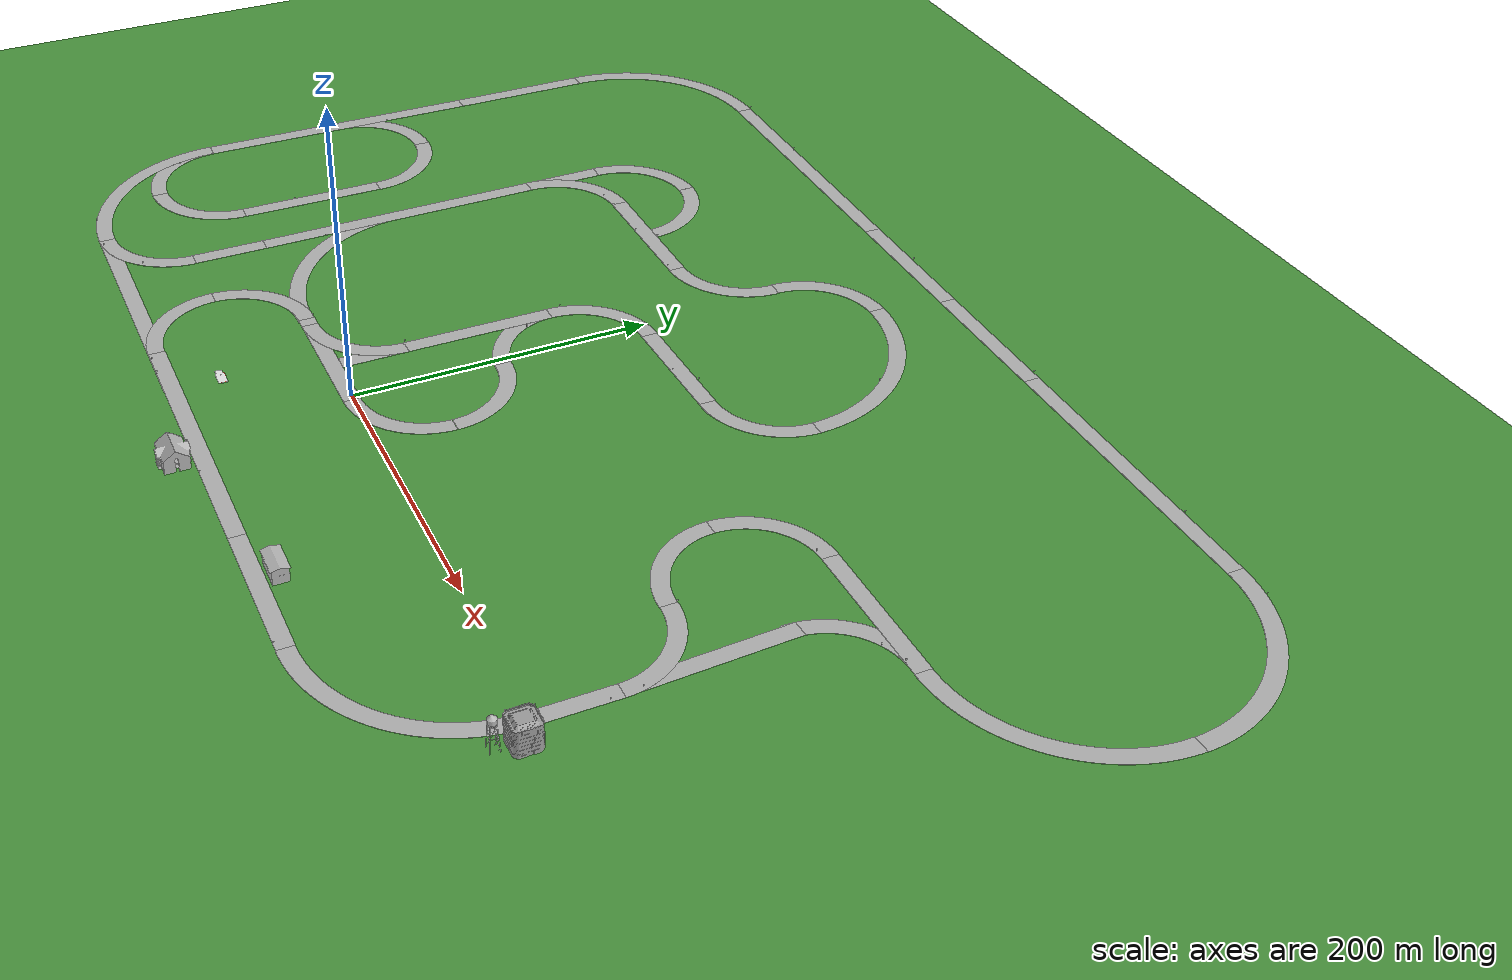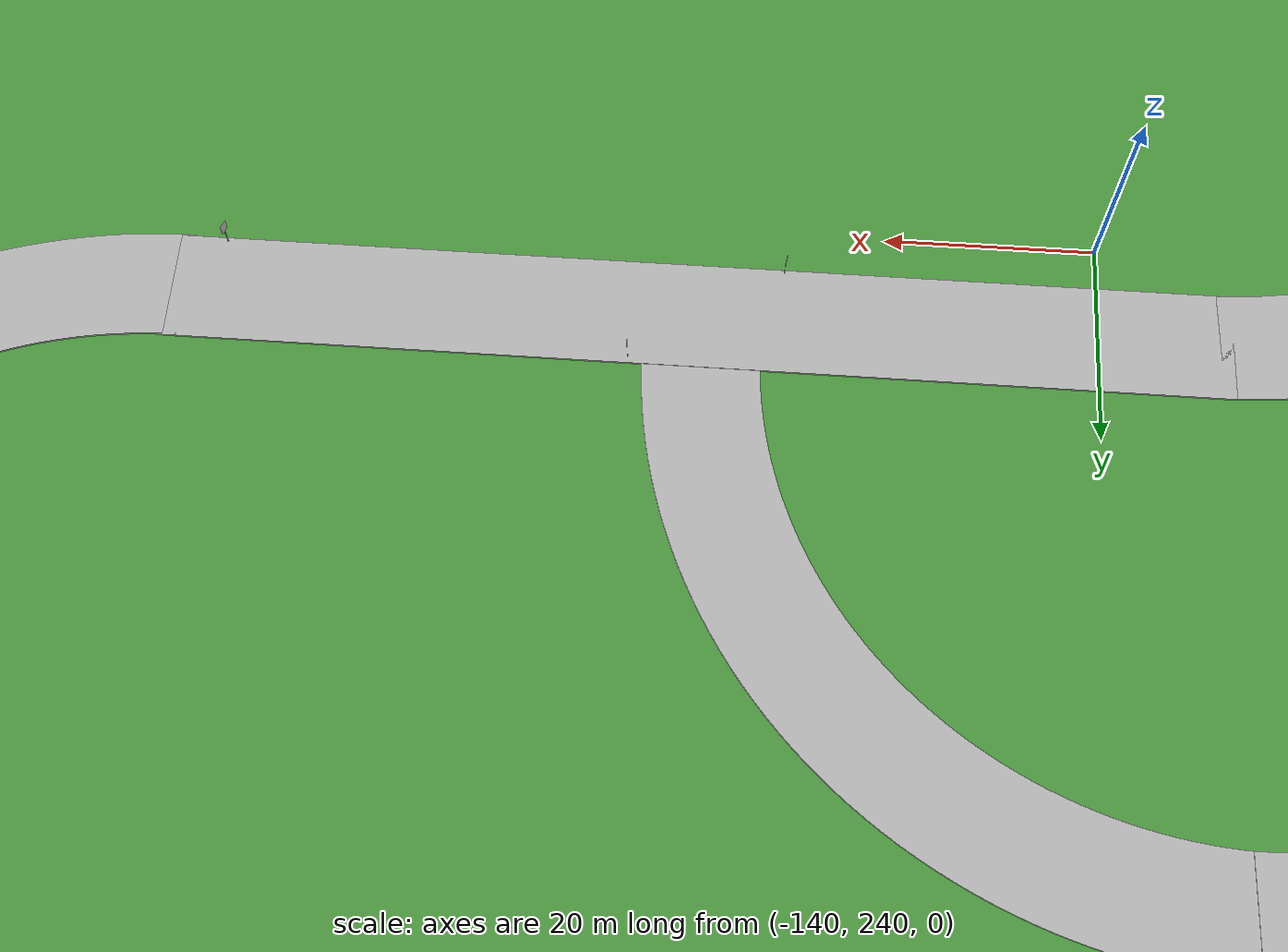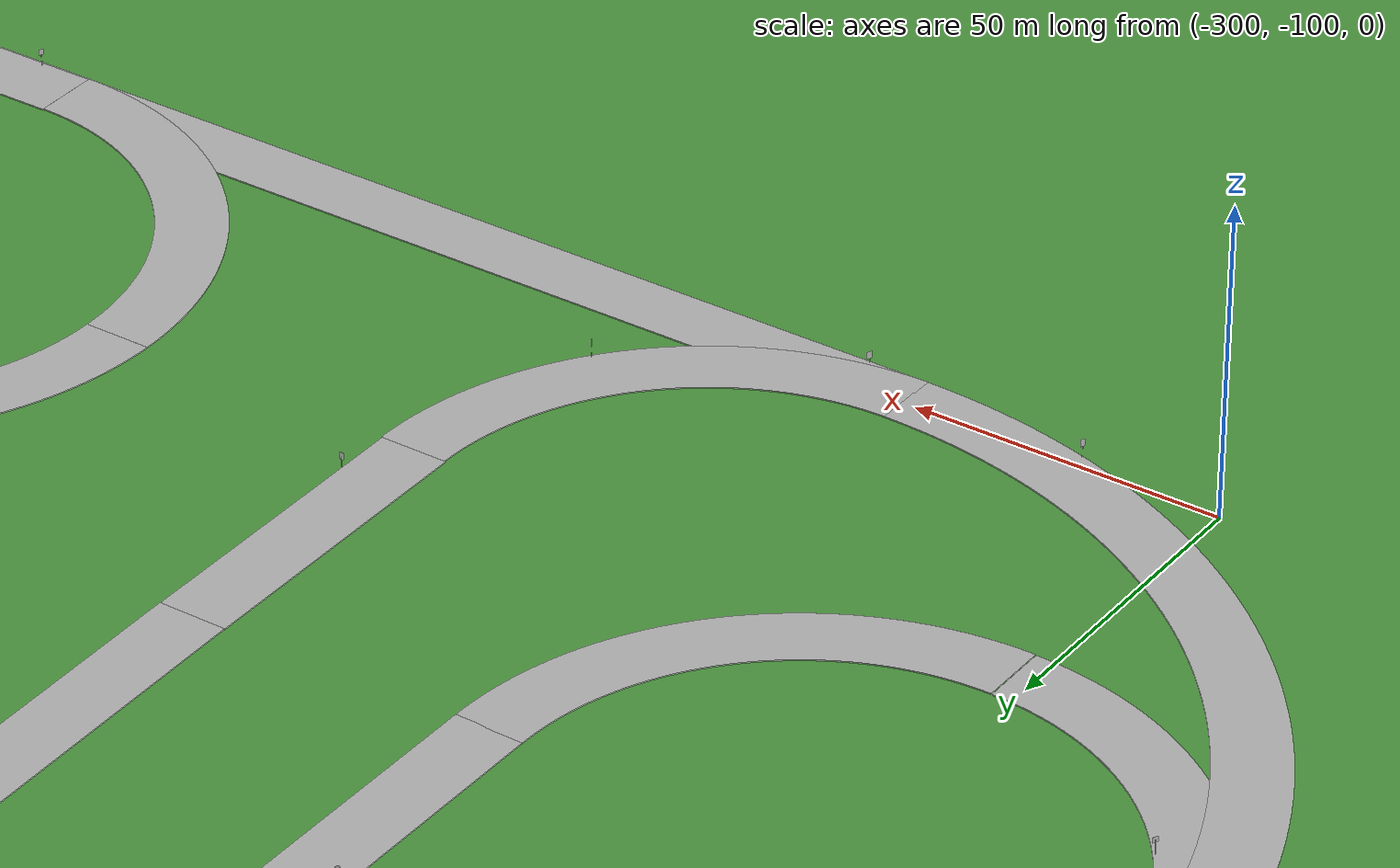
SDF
<sdf version="1.6">
 <world name="default">
  <light name="sun" type="directional">
   <pose>0 0 10 0 -0 0</pose>
   <diffuse>0.8 0.8 0.8 1</diffuse>
   <specular>0.2 0.2 0.2 1</specular>
   <attenuation>
    <range>1000</range>
    <constant>0.9</constant>
    <linear>0.01</linear>
    <quadratic>0.001</quadratic>
   </attenuation>
   <direction>-0.5 0.1 -0.9</direction>
  </light>
  <gravity>0 0 -9.8</gravity>
  <magnetic_field>6e-06 2.3e-05 -4.2e-05</magnetic_field>
  <atmosphere type="adiabatic"/>
  <physics name="default_physics" default="0" type="ode">
   <max_step_size>0.001</max_step_size>
   <real_time_factor>1</real_time_factor>
   <real_time_update_rate>1000</real_time_update_rate>
  </physics>
  <scene><ambient>0.4 0.4 0.4 1</ambient><background>0.7 0.7 0.7 1</background><shadows>1</shadows></scene>
  <audio><device>default</device></audio>
  <spherical_coordinates>
   <surface_model>EARTH_WGS84</surface_model>
   <latitude_deg>0</latitude_deg>
   <longitude_deg>0</longitude_deg>
   <elevation>0</elevation>
   <heading_deg>0</heading_deg>
  </spherical_coordinates>
  <model name="ground_plane">
   <static>1</static>
   <link name="link">
    <collision name="collision">
     <geometry><plane><normal>0 0 1</normal><size>10000 10000</size></plane></geometry>
     <surface><friction><ode><mu>100</mu><mu2>50</mu2></ode></friction></surface>
    </collision>
    <visual name="visual">
     <cast_shadows>0</cast_shadows>
     <geometry><plane><normal>0 0 1</normal><size>10000 10000</size></plane></geometry>
     <material>
      <script>
       <uri>model://ds_grass_background/materials/scripts</uri>
       <uri>model://ds_grass_background/materials/textures</uri>
       <name>GrassBackground</name>
      </script>
     </material>
    </visual>
    <velocity_decay><linear>0</linear><angular>0</angular></velocity_decay>
   </link>
  </model>
  <model name="Gas Station">
   <static>1</static>
   <link name="link">
    <collision name="collision">
     <geometry><mesh><uri>model://gas_station/meshes/gas_station.dae</uri></mesh></geometry>
    </collision>
    <visual name="visual">
     <geometry><mesh><uri>model://gas_station/meshes/gas_station.dae</uri></mesh></geometry>
     <material>
      <script>
       <uri>model://gas_station/materials/scripts</uri>
       <uri>model://gas_station/materials/textures</uri>
       <name>GasStation/Diffuse</name>
      </script>
      <shader type="normal_map_object_space"><normal_map>GasStation_Normal.png</normal_map></shader>
     </material>
    </visual>
   </link>
   <pose>-47.8817 -70.5161 0 0 -0 0</pose>
  </model>
  <model name="(DS) Straight Road - 200m_8">
   <static>1</static>
   <link name="link">
    <inertial>
     <mass>1</mass>
     <inertia><ixx>1</ixx><iyy>1</iyy><izz>1</izz><ixy>0</ixy><ixz>0</ixz><iyz>0</iyz></inertia>
    </inertial>
    <collision name="collision">
     <geometry><mesh><uri>model://ds_straight_road_200m/meshes/straight_road_200m.dae</uri></mesh></geometry>
    </collision>
    <visual name="visual">
     <geometry><mesh><uri>model://ds_straight_road_200m/meshes/straight_road_200m.dae</uri></mesh></geometry>
    </visual>
   </link>
   <pose>4.98041 -90.7828 0 0 -0 0</pose>
  </model>
  <model name="(DS) Straight Road - 100m_0">
   <static>1</static>
   <link name="link">
    <inertial>
     <mass>1</mass>
     <inertia><ixx>1</ixx><iyy>1</iyy><izz>1</izz><ixy>0</ixy><ixz>0</ixz><iyz>0</iyz></inertia>
    </inertial>
    <collision name="collision">
     <geometry><mesh><uri>model://ds_straight_road_100m/meshes/straight_road_100m.dae</uri></mesh></geometry>
    </collision>
    <visual name="visual">
     <geometry><mesh><uri>model://ds_straight_road_100m/meshes/straight_road_100m.dae</uri></mesh></geometry>
    </visual>
   </link>
   <pose>154.969 -90.7906 0 0 -0 0</pose>
  </model>
  <model name="(DS) Curved Road - 100m_3">
   <static>1</static>
   <link name="link">
    <inertial>
     <mass>1</mass>
     <inertia><ixx>1</ixx><iyy>1</iyy><izz>1</izz><ixy>0</ixy><ixz>0</ixz><iyz>0</iyz></inertia>
    </inertial>
    <collision name="collision">
     <geometry><mesh><uri>model://ds_curved_road_100m/meshes/curved_road_100m.dae</uri></mesh></geometry>
    </collision>
    <visual name="visual">
     <geometry><mesh><uri>model://ds_curved_road_100m/meshes/curved_road_100m.dae</uri></mesh></geometry>
    </visual>
   </link>
   <pose>257.705 -53.7644 0 0 -0 0</pose>
  </model>
  <model name="(DS) Straight Road - 50m">
   <static>1</static>
   <link name="link">
    <inertial>
     <mass>1</mass>
     <inertia><ixx>1</ixx><iyy>1</iyy><izz>1</izz><ixy>0</ixy><ixz>0</ixz><iyz>0</iyz></inertia>
    </inertial>
    <collision name="collision">
     <geometry><mesh><uri>model://ds_straight_road_50m/meshes/straight_road_50m.dae</uri></mesh></geometry>
    </collision>
    <visual name="visual">
     <geometry><mesh><uri>model://ds_straight_road_50m/meshes/straight_road_50m.dae</uri></mesh></geometry>
    </visual>
   </link>
   <pose>314.936 23.9712 0 0 0 -1.5707</pose>
  </model>
  <model name="(DS) Curved Road - 100m_7">
   <static>1</static>
   <link name="link">
    <inertial>
     <mass>1</mass>
     <inertia><ixx>1</ixx><iyy>1</iyy><izz>1</izz><ixy>0</ixy><ixz>0</ixz><iyz>0</iyz></inertia>
    </inertial>
    <collision name="collision">
     <geometry><mesh><uri>model://ds_curved_road_100m/meshes/curved_road_100m.dae</uri></mesh></geometry>
    </collision>
    <visual name="visual">
     <geometry><mesh><uri>model://ds_curved_road_100m/meshes/curved_road_100m.dae</uri></mesh></geometry>
    </visual>
   </link>
   <pose>-300.462 -53.7388 0 0 0 -1.5707</pose>
  </model>
  <model name="(DS) Straight Road - 50m_2">
   <static>1</static>
   <link name="link">
    <inertial>
     <mass>1</mass>
     <inertia><ixx>1</ixx><iyy>1</iyy><izz>1</izz><ixy>0</ixy><ixz>0</ixz><iyz>0</iyz></inertia>
    </inertial>
    <collision name="collision">
     <geometry><mesh><uri>model://ds_straight_road_50m/meshes/straight_road_50m.dae</uri></mesh></geometry>
    </collision>
    <visual name="visual">
     <geometry><mesh><uri>model://ds_straight_road_50m/meshes/straight_road_50m.dae</uri></mesh></geometry>
    </visual>
   </link>
   <pose>-208.133 -26.0849 0 0 -0 1.5707</pose>
  </model>
  <model name="(DS) Curved Road - 50m_1">
   <static>1</static>
   <link name="link">
    <inertial>
     <mass>1</mass>
     <inertia><ixx>1</ixx><iyy>1</iyy><izz>1</izz><ixy>0</ixy><ixz>0</ixz><iyz>0</iyz></inertia>
    </inertial>
    <collision name="collision">
     <geometry><mesh><uri>model://ds_curved_road_50m/meshes/curved_road_50m.dae</uri></mesh></geometry>
    </collision>
    <visual name="visual">
     <geometry><mesh><uri>model://ds_curved_road_50m/meshes/curved_road_50m.dae</uri></mesh></geometry>
    </visual>
   </link>
   <pose>-267.119 125.372 0 0 -0 1.5517</pose>
  </model>
  <model name="(DS) Curved Road - 50m_7">
   <static>1</static>
   <link name="link">
    <inertial>
     <mass>1</mass>
     <inertia><ixx>1</ixx><iyy>1</iyy><izz>1</izz><ixy>0</ixy><ixz>0</ixz><iyz>0</iyz></inertia>
    </inertial>
    <collision name="collision">
     <geometry><mesh><uri>model://ds_curved_road_50m/meshes/curved_road_50m.dae</uri></mesh></geometry>
    </collision>
    <visual name="visual">
     <geometry><mesh><uri>model://ds_curved_road_50m/meshes/curved_road_50m.dae</uri></mesh></geometry>
    </visual>
   </link>
   <pose>282.694 76.6819 0 0 -0 1.5707</pose>
  </model>
  <model name="(DS) Curved Road - 50m_8">
   <static>1</static>
   <link name="link">
    <inertial>
     <mass>1</mass>
     <inertia><ixx>1</ixx><iyy>1</iyy><izz>1</izz><ixy>0</ixy><ixz>0</ixz><iyz>0</iyz></inertia>
    </inertial>
    <collision name="collision">
     <geometry><mesh><uri>model://ds_curved_road_50m/meshes/curved_road_50m.dae</uri></mesh></geometry>
    </collision>
    <visual name="visual">
     <geometry><mesh><uri>model://ds_curved_road_50m/meshes/curved_road_50m.dae</uri></mesh></geometry>
    </visual>
   </link>
   <pose>227.233 176.317 0 0 -0 3.14159</pose>
  </model>
  <model name="(DS) Curved Road - 50m_9">
   <static>1</static>
   <link name="link">
    <inertial>
     <mass>1</mass>
     <inertia><ixx>1</ixx><iyy>1</iyy><izz>1</izz><ixy>0</ixy><ixz>0</ixz><iyz>0</iyz></inertia>
    </inertial>
    <collision name="collision">
     <geometry><mesh><uri>model://ds_curved_road_50m/meshes/curved_road_50m.dae</uri></mesh></geometry>
    </collision>
    <visual name="visual">
     <geometry><mesh><uri>model://ds_curved_road_50m/meshes/curved_road_50m.dae</uri></mesh></geometry>
    </visual>
   </link>
   <pose>227.236 120.969 0 0 0 -1.5707</pose>
  </model>
  <model name="(DS) Straight Road - 100m_6">
   <static>1</static>
   <link name="link">
    <inertial>
     <mass>1</mass>
     <inertia><ixx>1</ixx><iyy>1</iyy><izz>1</izz><ixy>0</ixy><ixz>0</ixz><iyz>0</iyz></inertia>
    </inertial>
    <collision name="collision">
     <geometry><mesh><uri>model://ds_straight_road_100m/meshes/straight_road_100m.dae</uri></mesh></geometry>
    </collision>
    <visual name="visual">
     <geometry><mesh><uri>model://ds_straight_road_100m/meshes/straight_road_100m.dae</uri></mesh></geometry>
    </visual>
   </link>
   <pose>304.773 208.555 0 0 -0 0</pose>
  </model>
  <model name="(DS) Curved Road - 100m_8">
   <static>1</static>
   <link name="link">
    <inertial>
     <mass>1</mass>
     <inertia><ixx>1</ixx><iyy>1</iyy><izz>1</izz><ixy>0</ixy><ixz>0</ixz><iyz>0</iyz></inertia>
    </inertial>
    <collision name="collision">
     <geometry><mesh><uri>model://ds_curved_road_100m/meshes/curved_road_100m.dae</uri></mesh></geometry>
    </collision>
    <visual name="visual">
     <geometry><mesh><uri>model://ds_curved_road_100m/meshes/curved_road_100m.dae</uri></mesh></geometry>
    </visual>
   </link>
   <pose>407.453 245.59 0 0 -0 0</pose>
  </model>
  <model name="(DS) Curved Road - 100m_10">
   <static>1</static>
   <link name="link">
    <inertial>
     <mass>1</mass>
     <inertia><ixx>1</ixx><iyy>1</iyy><izz>1</izz><ixy>0</ixy><ixz>0</ixz><iyz>0</iyz></inertia>
    </inertial>
    <collision name="collision">
     <geometry><mesh><uri>model://ds_curved_road_100m/meshes/curved_road_100m.dae</uri></mesh></geometry>
    </collision>
    <visual name="visual">
     <geometry><mesh><uri>model://ds_curved_road_100m/meshes/curved_road_100m.dae</uri></mesh></geometry>
    </visual>
   </link>
   <pose>-297.976 351.025 0 0 -0 3.14153</pose>
  </model>
  <model name="(DS) Curved Road - 100m_11">
   <static>1</static>
   <link name="link">
    <inertial>
     <mass>1</mass>
     <inertia><ixx>1</ixx><iyy>1</iyy><izz>1</izz><ixy>0</ixy><ixz>0</ixz><iyz>0</iyz></inertia>
    </inertial>
    <collision name="collision">
     <geometry><mesh><uri>model://ds_curved_road_100m/meshes/curved_road_100m.dae</uri></mesh></geometry>
    </collision>
    <visual name="visual">
     <geometry><mesh><uri>model://ds_curved_road_100m/meshes/curved_road_100m.dae</uri></mesh></geometry>
    </visual>
   </link>
   <pose>407.577 351.04 0 0 -0 1.5707</pose>
  </model>
  <model name="(DS) Straight Road - 200m_9">
   <static>1</static>
   <link name="link">
    <inertial>
     <mass>1</mass>
     <inertia><ixx>1</ixx><iyy>1</iyy><izz>1</izz><ixy>0</ixy><ixz>0</ixz><iyz>0</iyz></inertia>
    </inertial>
    <collision name="collision">
     <geometry><mesh><uri>model://ds_straight_road_200m/meshes/straight_road_200m.dae</uri></mesh></geometry>
    </collision>
    <visual name="visual">
     <geometry><mesh><uri>model://ds_straight_road_200m/meshes/straight_road_200m.dae</uri></mesh></geometry>
    </visual>
   </link>
   <pose>-145.191 408.281 0 0 -0 0</pose>
  </model>
  <model name="(DS) Straight Road - 200m_11">
   <static>1</static>
   <link name="link">
    <inertial>
     <mass>1</mass>
     <inertia><ixx>1</ixx><iyy>1</iyy><izz>1</izz><ixy>0</ixy><ixz>0</ixz><iyz>0</iyz></inertia>
    </inertial>
    <collision name="collision">
     <geometry><mesh><uri>model://ds_straight_road_200m/meshes/straight_road_200m.dae</uri></mesh></geometry>
    </collision>
    <visual name="visual">
     <geometry><mesh><uri>model://ds_straight_road_200m/meshes/straight_road_200m.dae</uri></mesh></geometry>
    </visual>
   </link>
   <pose>254.821 408.288 0 0 -0 0</pose>
  </model>
  <model name="(DS) Curved Road - 50m_12">
   <static>1</static>
   <link name="link">
    <inertial>
     <mass>1</mass>
     <inertia><ixx>1</ixx><iyy>1</iyy><izz>1</izz><ixy>0</ixy><ixz>0</ixz><iyz>0</iyz></inertia>
    </inertial>
    <collision name="collision">
     <geometry><mesh><uri>model://ds_curved_road_50m/meshes/curved_road_50m.dae</uri></mesh></geometry>
    </collision>
    <visual name="visual">
     <geometry><mesh><uri>model://ds_curved_road_50m/meshes/curved_road_50m.dae</uri></mesh></geometry>
    </visual>
   </link>
   <pose>18.1266 326.932 0 0 -0 3.13988</pose>
  </model>
  <model name="(DS) Straight Road - 100m_8">
   <static>1</static>
   <link name="link">
    <inertial>
     <mass>1</mass>
     <inertia><ixx>1</ixx><iyy>1</iyy><izz>1</izz><ixy>0</ixy><ixz>0</ixz><iyz>0</iyz></inertia>
    </inertial>
    <collision name="collision">
     <geometry><mesh><uri>model://ds_straight_road_100m/meshes/straight_road_100m.dae</uri></mesh></geometry>
    </collision>
    <visual name="visual">
     <geometry><mesh><uri>model://ds_straight_road_100m/meshes/straight_road_100m.dae</uri></mesh></geometry>
    </visual>
   </link>
   <pose>55.7639 209.318 -0.024663 0 -0 0.020634</pose>
  </model>
  <model name="speed_25">
   <link name="link">
    <collision name="collision">
     <geometry><mesh><scale>1 1 1</scale><uri>model://speed_25/meshes/speedlim_25.dae</uri></mesh></geometry>
    </collision>
    <visual name="visual">
     <geometry><mesh><scale>1 1 1</scale><uri>model://speed_25/meshes/speedlim_25.dae</uri></mesh></geometry>
    </visual>
    <inertial>
     <inertia><ixx>1</ixx><ixy>0</ixy><ixz>0</ixz><iyy>1</iyy><iyz>0</iyz><izz>1</izz></inertia>
     <mass>1</mass>
    </inertial>
   </link>
   <pose>-71.1839 -106.087 0.102221 2e-06 -2e-06 2.99398</pose>
  </model>
  <model name="speed_10">
   <link name="link">
    <collision name="collision">
     <geometry><mesh><scale>1 1 1</scale><uri>model://speed_10/meshes/speedlim_10.dae</uri></mesh></geometry>
    </collision>
    <visual name="visual">
     <geometry><mesh><scale>1 1 1</scale><uri>model://speed_10/meshes/speedlim_10.dae</uri></mesh></geometry>
    </visual>
    <inertial>
     <inertia><ixx>1</ixx><ixy>0</ixy><ixz>0</ixz><iyy>1</iyy><iyz>0</iyz><izz>1</izz></inertia>
     <mass>1</mass>
    </inertial>
   </link>
   <pose>200.707 -106.096 0.102229 2e-06 -1e-06 3.10057</pose>
  </model>
  <model name="speed_10_0">
   <link name="link">
    <collision name="collision">
     <geometry><mesh><scale>1 1 1</scale><uri>model://speed_10/meshes/speedlim_10.dae</uri></mesh></geometry>
    </collision>
    <visual name="visual">
     <geometry><mesh><scale>1 1 1</scale><uri>model://speed_10/meshes/speedlim_10.dae</uri></mesh></geometry>
    </visual>
    <inertial>
     <inertia><ixx>1</ixx><ixy>0</ixy><ixz>0</ixz><iyy>1</iyy><iyz>0</iyz><izz>1</izz></inertia>
     <mass>1</mass>
    </inertial>
   </link>
   <pose>310.131 40.5807 0.102221 2e-06 -2e-06 -1.63806</pose>
  </model>
  <model name="speed_15">
   <link name="link">
    <collision name="collision">
     <geometry><mesh><scale>1 1 1</scale><uri>model://speed_15/meshes/speedlim_15.dae</uri></mesh></geometry>
    </collision>
    <visual name="visual">
     <geometry><mesh><scale>1 1 1</scale><uri>model://speed_15/meshes/speedlim_15.dae</uri></mesh></geometry>
    </visual>
    <inertial>
     <inertia><ixx>1</ixx><ixy>0</ixy><ixz>0</ixz><iyy>1</iyy><iyz>0</iyz><izz>1</izz></inertia>
     <mass>1</mass>
    </inertial>
   </link>
   <pose>248.816 193.12 0.102229 2e-06 -1e-06 3.12856</pose>
  </model>
  <model name="speed_10_1">
   <link name="link">
    <collision name="collision">
     <geometry><mesh><scale>1 1 1</scale><uri>model://speed_10/meshes/speedlim_10.dae</uri></mesh></geometry>
    </collision>
    <visual name="visual">
     <geometry><mesh><scale>1 1 1</scale><uri>model://speed_10/meshes/speedlim_10.dae</uri></mesh></geometry>
    </visual>
    <inertial>
     <inertia><ixx>1</ixx><ixy>0</ixy><ixz>0</ixz><iyy>1</iyy><iyz>0</iyz><izz>1</izz></inertia>
     <mass>1</mass>
    </inertial>
   </link>
   <pose>345.442 193.311 0.102221 2e-06 -2e-06 2.65487</pose>
  </model>
  <model name="(DS) Straight Road - 100m">
   <static>1</static>
   <link name="link">
    <inertial>
     <mass>1</mass>
     <inertia><ixx>1</ixx><iyy>1</iyy><izz>1</izz><ixy>0</ixy><ixz>0</ixz><iyz>0</iyz></inertia>
    </inertial>
    <collision name="collision">
     <geometry><mesh><uri>model://ds_straight_road_100m/meshes/straight_road_100m.dae</uri></mesh></geometry>
    </collision>
    <visual name="visual">
     <geometry><mesh><uri>model://ds_straight_road_100m/meshes/straight_road_100m.dae</uri></mesh></geometry>
    </visual>
   </link>
   <pose>4.74209 408.294 0 0 -0 0</pose>
  </model>
  <model name="(DS) Straight Road - 100m_1">
   <static>1</static>
   <link name="link">
    <inertial>
     <mass>1</mass>
     <inertia><ixx>1</ixx><iyy>1</iyy><izz>1</izz><ixy>0</ixy><ixz>0</ixz><iyz>0</iyz></inertia>
    </inertial>
    <collision name="collision">
     <geometry><mesh><uri>model://ds_straight_road_100m/meshes/straight_road_100m.dae</uri></mesh></geometry>
    </collision>
    <visual name="visual">
     <geometry><mesh><uri>model://ds_straight_road_100m/meshes/straight_road_100m.dae</uri></mesh></geometry>
    </visual>
   </link>
   <pose>104.772 408.244 0 0 -0 0</pose>
  </model>
  <model name="(DS) Straight Road - 100m_2">
   <static>1</static>
   <link name="link">
    <inertial>
     <mass>1</mass>
     <inertia><ixx>1</ixx><iyy>1</iyy><izz>1</izz><ixy>0</ixy><ixz>0</ixz><iyz>0</iyz></inertia>
    </inertial>
    <collision name="collision">
     <geometry><mesh><uri>model://ds_straight_road_100m/meshes/straight_road_100m.dae</uri></mesh></geometry>
    </collision>
    <visual name="visual">
     <geometry><mesh><uri>model://ds_straight_road_100m/meshes/straight_road_100m.dae</uri></mesh></geometry>
    </visual>
   </link>
   <pose>-335.161 248.375 0 0 0 -1.57376</pose>
  </model>
  <model name="(DS) Straight Road - 200m">
   <static>1</static>
   <link name="link">
    <inertial>
     <mass>1</mass>
     <inertia><ixx>1</ixx><iyy>1</iyy><izz>1</izz><ixy>0</ixy><ixz>0</ixz><iyz>0</iyz></inertia>
    </inertial>
    <collision name="collision">
     <geometry><mesh><uri>model://ds_straight_road_200m/meshes/straight_road_200m.dae</uri></mesh></geometry>
    </collision>
    <visual name="visual">
     <geometry><mesh><uri>model://ds_straight_road_200m/meshes/straight_road_200m.dae</uri></mesh></geometry>
    </visual>
   </link>
   <pose>-336.34 98.3301 0 0 0 -1.58132</pose>
  </model>
  <model name="(DS) Curved Road - 50m">
   <static>1</static>
   <link name="link">
    <inertial>
     <mass>1</mass>
     <inertia><ixx>1</ixx><iyy>1</iyy><izz>1</izz><ixy>0</ixy><ixz>0</ixz><iyz>0</iyz></inertia>
    </inertial>
    <collision name="collision">
     <geometry><mesh><uri>model://ds_curved_road_50m/meshes/curved_road_50m.dae</uri></mesh></geometry>
    </collision>
    <visual name="visual">
     <geometry><mesh><uri>model://ds_curved_road_50m/meshes/curved_road_50m.dae</uri></mesh></geometry>
    </visual>
   </link>
   <pose>-220.18 -78.7697 0 0 -0 0</pose>
  </model>
  <model name="(DS) Curved Road - 50m_0">
   <static>1</static>
   <link name="link">
    <inertial>
     <mass>1</mass>
     <inertia><ixx>1</ixx><iyy>1</iyy><izz>1</izz><ixy>0</ixy><ixz>0</ixz><iyz>0</iyz></inertia>
    </inertial>
    <collision name="collision">
     <geometry><mesh><uri>model://ds_curved_road_50m/meshes/curved_road_50m.dae</uri></mesh></geometry>
    </collision>
    <visual name="visual">
     <geometry><mesh><uri>model://ds_curved_road_50m/meshes/curved_road_50m.dae</uri></mesh></geometry>
    </visual>
   </link>
   <pose>-178.668 226.66 0 0 -0 -3.1191</pose>
  </model>
  <model name="(DS) Curved Road - 50m_2">
   <static>1</static>
   <link name="link">
    <inertial>
     <mass>1</mass>
     <inertia><ixx>1</ixx><iyy>1</iyy><izz>1</izz><ixy>0</ixy><ixz>0</ixz><iyz>0</iyz></inertia>
    </inertial>
    <collision name="collision">
     <geometry><mesh><uri>model://ds_curved_road_50m/meshes/curved_road_50m.dae</uri></mesh></geometry>
    </collision>
    <visual name="visual">
     <geometry><mesh><uri>model://ds_curved_road_50m/meshes/curved_road_50m.dae</uri></mesh></geometry>
    </visual>
   </link>
   <pose>32.0995 20.9526 0 0 -0 0</pose>
  </model>
  <model name="(DS) Straight Road - 100m_3">
   <static>1</static>
   <link name="link">
    <inertial>
     <mass>1</mass>
     <inertia><ixx>1</ixx><iyy>1</iyy><izz>1</izz><ixy>0</ixy><ixz>0</ixz><iyz>0</iyz></inertia>
    </inertial>
    <collision name="collision">
     <geometry><mesh><uri>model://ds_straight_road_100m/meshes/straight_road_100m.dae</uri></mesh></geometry>
    </collision>
    <visual name="visual">
     <geometry><mesh><uri>model://ds_straight_road_100m/meshes/straight_road_100m.dae</uri></mesh></geometry>
    </visual>
   </link>
   <pose>-45.6446 8.79709 -0.026822 0 -0 0</pose>
  </model>
  <model name="(DS) Curved Road - 50m_4">
   <static>1</static>
   <link name="link">
    <inertial>
     <mass>1</mass>
     <inertia><ixx>1</ixx><iyy>1</iyy><izz>1</izz><ixy>0</ixy><ixz>0</ixz><iyz>0</iyz></inertia>
    </inertial>
    <collision name="collision">
     <geometry><mesh><uri>model://ds_curved_road_50m/meshes/curved_road_50m.dae</uri></mesh></geometry>
    </collision>
    <visual name="visual">
     <geometry><mesh><uri>model://ds_curved_road_50m/meshes/curved_road_50m.dae</uri></mesh></geometry>
    </visual>
   </link>
   <pose>-122.795 -78.7138 0 0 0 -1.5704</pose>
  </model>
  <model name="(DS) Curved Road - 50m_5">
   <static>1</static>
   <link name="link">
    <inertial>
     <mass>1</mass>
     <inertia><ixx>1</ixx><iyy>1</iyy><izz>1</izz><ixy>0</ixy><ixz>0</ixz><iyz>0</iyz></inertia>
    </inertial>
    <collision name="collision">
     <geometry><mesh><uri>model://ds_curved_road_50m/meshes/curved_road_50m.dae</uri></mesh></geometry>
    </collision>
    <visual name="visual">
     <geometry><mesh><uri>model://ds_curved_road_50m/meshes/curved_road_50m.dae</uri></mesh></geometry>
    </visual>
   </link>
   <pose>-122.722 -23.3126 0 0 -0 3.13868</pose>
  </model>
  <model name="(DS) Curved Road - 50m_6">
   <static>1</static>
   <link name="link">
    <inertial>
     <mass>1</mass>
     <inertia><ixx>1</ixx><iyy>1</iyy><izz>1</izz><ixy>0</ixy><ixz>0</ixz><iyz>0</iyz></inertia>
    </inertial>
    <collision name="collision">
     <geometry><mesh><uri>model://ds_curved_road_50m/meshes/curved_road_50m.dae</uri></mesh></geometry>
    </collision>
    <visual name="visual">
     <geometry><mesh><uri>model://ds_curved_road_50m/meshes/curved_road_50m.dae</uri></mesh></geometry>
    </visual>
   </link>
   <pose>123.091 222.001 0 0 0 -0.008161</pose>
  </model>
  <model name="apartment">
   <static>1</static>
   <link name="link">
    <collision name="collision">
     <geometry><mesh><uri>model://apartment/meshes/apartment.dae</uri></mesh></geometry>
    </collision>
    <visual name="visual">
     <geometry><mesh><uri>model://apartment/meshes/apartment.dae</uri></mesh></geometry>
    </visual>
   </link>
   <pose>22.467 -117.335 0 0 0 -1.56402</pose>
  </model>
  <model name="fire_station">
   <static>1</static>
   <link name="link">
    <collision name="main">
     <pose>0 -0.135 5 0 -0 0</pose>
     <geometry><box><size>19.98 9.68 10</size></box></geometry>
    </collision>
    <collision name="front_top">
     <pose>0 4.957 7 0 -0 0</pose>
     <geometry><box><size>20 0.515 6</size></box></geometry>
    </collision>
    <collision name="column_0">
     <pose>9.333 4.957 2 0 -0 0</pose>
     <geometry><box><size>1.315 0.515 4</size></box></geometry>
    </collision>
    <collision name="column_1">
     <pose>3.33 4.957 2 0 -0 0</pose>
     <geometry><box><size>2.63 0.515 4</size></box></geometry>
    </collision>
    <collision name="column_2">
     <pose>-3.33 4.957 2 0 -0 0</pose>
     <geometry><box><size>2.63 0.515 4</size></box></geometry>
    </collision>
    <collision name="column_3">
     <pose>-9.333 4.957 2 0 -0 0</pose>
     <geometry><box><size>1.315 0.515 4</size></box></geometry>
    </collision>
    <collision name="roof_back">
     <pose>0 -2.742 10.467 0.25 -0 0</pose>
     <geometry><box><size>21.47 6.12 0.28</size></box></geometry>
    </collision>
    <collision name="roof_front">
     <pose>0 3.12 10.467 -0.25 0 0</pose>
     <geometry><box><size>21.47 6.12 0.28</size></box></geometry>
    </collision>
    <collision name="roof_base">
     <pose>0 0.188 9.705 0 -0 0</pose>
     <geometry><box><size>21.47 11.86 0.28</size></box></geometry>
    </collision>
    <collision name="roof_filling_0">
     <pose>0 0.188 9.985 0 -0 0</pose>
     <geometry><box><size>21.47 9.53 0.28</size></box></geometry>
    </collision>
    <collision name="roof_filling_1">
     <pose>0 0.188 10.14 0 -0 0</pose>
     <geometry><box><size>21.47 8.41 0.28</size></box></geometry>
    </collision>
    <collision name="roof_filling_2">
     <pose>0 0.188 10.42 0 -0 0</pose>
     <geometry><box><size>21.47 6.25 0.28</size></box></geometry>
    </collision>
    <collision name="roof_filling_3">
     <pose>0 0.188 10.7 0 -0 0</pose>
     <geometry><box><size>21.47 4.05 0.28</size></box></geometry>
    </collision>
    <collision name="roof_filling_4">
     <pose>0 0.188 10.98 0 -0 0</pose>
     <geometry><box><size>21.47 1.83 0.28</size></box></geometry>
    </collision>
    <visual name="visual">
     <geometry><mesh><uri>model://fire_station/meshes/fire_station.dae</uri></mesh></geometry>
    </visual>
   </link>
   <pose>144.432 -88.6776 0 0 -0 0</pose>
  </model>
  <model name="Office Building">
   <static>1</static>
   <link name="link">
    <collision name="collision">
     <geometry><mesh><uri>model://office_building/meshes/office_building.dae</uri></mesh></geometry>
    </collision>
    <visual name="visual">
     <geometry><mesh><uri>model://office_building/meshes/office_building.dae</uri></mesh></geometry>
    </visual>
   </link>
   <pose>319.671 -10.8293 0 0 -0 0</pose>
  </model>
  <model name="water_tower">
   <static>1</static>
   <link name="link">
    <collision name="collision">
     <geometry><mesh><uri>model://water_tower/meshes/water_tower.dae</uri></mesh></geometry>
    </collision>
    <visual name="visual">
     <geometry><mesh><uri>model://water_tower/meshes/water_tower.dae</uri></mesh></geometry>
    </visual>
   </link>
   <pose>317.064 -26.4081 0 0 -0 0</pose>
  </model>
  <model name="stop">
   <link name="link">
    <collision name="collision">
     <geometry><mesh><scale>1 1 1</scale><uri>model://stop/meshes/stop.dae</uri></mesh></geometry>
    </collision>
    <visual name="visual">
     <geometry><mesh><scale>1 1 1</scale><uri>model://stop/meshes/stop.dae</uri></mesh></geometry>
    </visual>
    <inertial>
     <inertia><ixx>1</ixx><ixy>0</ixy><ixz>0</ixz><iyy>1</iyy><iyz>0</iyz><izz>1</izz></inertia>
     <mass>1</mass>
    </inertial>
   </link>
   <pose>8.11745 -105.858 0.102221 2e-06 -2e-06 2.93218</pose>
  </model>
  <model name="speed_20">
   <link name="link">
    <collision name="collision">
     <geometry><mesh><scale>1 1 1</scale><uri>model://speed_20/meshes/speedlim_20.dae</uri></mesh></geometry>
    </collision>
    <visual name="visual">
     <geometry><mesh><scale>1 1 1</scale><uri>model://speed_20/meshes/speedlim_20.dae</uri></mesh></geometry>
    </visual>
    <inertial>
     <inertia><ixx>1</ixx><ixy>0</ixy><ixz>0</ixz><iyy>1</iyy><iyz>0</iyz><izz>1</izz></inertia>
     <mass>1</mass>
    </inertial>
   </link>
   <pose>40.6512 -106.177 0.102221 2e-06 -2e-06 2.95184</pose>
  </model>
  <model name="(DS) Straight Road - 100m_4">
   <static>1</static>
   <link name="link">
    <inertial>
     <mass>1</mass>
     <inertia><ixx>1</ixx><iyy>1</iyy><izz>1</izz><ixy>0</ixy><ixz>0</ixz><iyz>0</iyz></inertia>
    </inertial>
    <collision name="collision">
     <geometry><mesh><uri>model://ds_straight_road_100m/meshes/straight_road_100m.dae</uri></mesh></geometry>
    </collision>
    <visual name="visual">
     <geometry><mesh><uri>model://ds_straight_road_100m/meshes/straight_road_100m.dae</uri></mesh></geometry>
    </visual>
   </link>
   <pose>312.272 105.889 -0.032356 0 0 -1.52847</pose>
  </model>
  <model name="left_turn_only">
   <link name="link">
    <collision name="collision">
     <geometry>
      <mesh><scale>1 1 1</scale><uri>model://left_turn_only/meshes/left_turn_only.dae</uri></mesh>
     </geometry>
    </collision>
    <visual name="visual">
     <geometry>
      <mesh><scale>1 1 1</scale><uri>model://left_turn_only/meshes/left_turn_only.dae</uri></mesh>
     </geometry>
    </visual>
    <inertial>
     <inertia><ixx>1</ixx><ixy>0</ixy><ixz>0</ixz><iyy>1</iyy><iyz>0</iyz><izz>1</izz></inertia>
     <mass>1</mass>
    </inertial>
   </link>
   <pose>308.368 59.881 0.102229 2e-06 -1e-06 -1.76523</pose>
  </model>
  <model name="(DS) Curved Road - 50m_10">
   <static>1</static>
   <link name="link">
    <inertial>
     <mass>1</mass>
     <inertia><ixx>1</ixx><iyy>1</iyy><izz>1</izz><ixy>0</ixy><ixz>0</ixz><iyz>0</iyz></inertia>
    </inertial>
    <collision name="collision">
     <geometry><mesh><uri>model://ds_curved_road_50m/meshes/curved_road_50m.dae</uri></mesh></geometry>
    </collision>
    <visual name="visual">
     <geometry><mesh><uri>model://ds_curved_road_50m/meshes/curved_road_50m.dae</uri></mesh></geometry>
    </visual>
   </link>
   <pose>320.736 175.053 -0.078351 0 0 -3.09893</pose>
  </model>
  <model name="yield">
   <link name="link">
    <collision name="collision">
     <geometry><mesh><scale>1 1 1</scale><uri>model://yield/meshes/yield.dae</uri></mesh></geometry>
    </collision>
    <visual name="visual">
     <geometry><mesh><scale>1 1 1</scale><uri>model://yield/meshes/yield.dae</uri></mesh></geometry>
    </visual>
    <inertial>
     <inertia><ixx>1</ixx><ixy>0</ixy><ixz>0</ixz><iyy>1</iyy><iyz>0</iyz><izz>1</izz></inertia>
     <mass>1</mass>
    </inertial>
   </link>
   <pose>329.092 188.373 0.02387 2e-06 -2e-06 -2.80019</pose>
  </model>
  <model name="speed_10_2">
   <link name="link">
    <collision name="collision">
     <geometry><mesh><scale>1 1 1</scale><uri>model://speed_10/meshes/speedlim_10.dae</uri></mesh></geometry>
    </collision>
    <visual name="visual">
     <geometry><mesh><scale>1 1 1</scale><uri>model://speed_10/meshes/speedlim_10.dae</uri></mesh></geometry>
    </visual>
    <inertial>
     <inertia><ixx>1</ixx><ixy>0</ixy><ixz>0</ixz><iyy>1</iyy><iyz>0</iyz><izz>1</izz></inertia>
     <mass>1</mass>
    </inertial>
   </link>
   <pose>256.248 103.599 0.102221 2e-06 -2e-06 -0.373289</pose>
  </model>
  <model name="speed_10_3">
   <link name="link">
    <collision name="collision">
     <geometry><mesh><scale>1 1 1</scale><uri>model://speed_10/meshes/speedlim_10.dae</uri></mesh></geometry>
    </collision>
    <visual name="visual">
     <geometry><mesh><scale>1 1 1</scale><uri>model://speed_10/meshes/speedlim_10.dae</uri></mesh></geometry>
    </visual>
    <inertial>
     <inertia><ixx>1</ixx><ixy>0</ixy><ixz>0</ixz><iyy>1</iyy><iyz>0</iyz><izz>1</izz></inertia>
     <mass>1</mass>
    </inertial>
   </link>
   <pose>459.391 309.942 0.102221 2e-06 -2e-06 -1.88882</pose>
  </model>
  <model name="speed_15_0">
   <link name="link">
    <collision name="collision">
     <geometry><mesh><scale>1 1 1</scale><uri>model://speed_15/meshes/speedlim_15.dae</uri></mesh></geometry>
    </collision>
    <visual name="visual">
     <geometry><mesh><scale>1 1 1</scale><uri>model://speed_15/meshes/speedlim_15.dae</uri></mesh></geometry>
    </visual>
    <inertial>
     <inertia><ixx>1</ixx><ixy>0</ixy><ixz>0</ixz><iyy>1</iyy><iyz>0</iyz><izz>1</izz></inertia>
     <mass>1</mass>
    </inertial>
   </link>
   <pose>378.845 400.508 0.102221 2e-06 -2e-06 -0.579735</pose>
  </model>
  <model name="speed_25_0">
   <link name="link">
    <collision name="collision">
     <geometry><mesh><scale>1 1 1</scale><uri>model://speed_25/meshes/speedlim_25.dae</uri></mesh></geometry>
    </collision>
    <visual name="visual">
     <geometry><mesh><scale>1 1 1</scale><uri>model://speed_25/meshes/speedlim_25.dae</uri></mesh></geometry>
    </visual>
    <inertial>
     <inertia><ixx>1</ixx><ixy>0</ixy><ixz>0</ixz><iyy>1</iyy><iyz>0</iyz><izz>1</izz></inertia>
     <mass>1</mass>
    </inertial>
   </link>
   <pose>303.049 403.28 0.102229 2e-06 -1e-06 1.8e-05</pose>
  </model>
  <model name="speed_25_1">
   <link name="link">
    <collision name="collision">
     <geometry><mesh><scale>1 1 1</scale><uri>model://speed_25/meshes/speedlim_25.dae</uri></mesh></geometry>
    </collision>
    <visual name="visual">
     <geometry><mesh><scale>1 1 1</scale><uri>model://speed_25/meshes/speedlim_25.dae</uri></mesh></geometry>
    </visual>
    <inertial>
     <inertia><ixx>1</ixx><ixy>0</ixy><ixz>0</ixz><iyy>1</iyy><iyz>0</iyz><izz>1</izz></inertia>
     <mass>1</mass>
    </inertial>
   </link>
   <pose>149.917 403.321 0.102221 2e-06 -2e-06 2.8e-05</pose>
  </model>
  <model name="speed_25_2">
   <link name="link">
    <collision name="collision">
     <geometry><mesh><scale>1 1 1</scale><uri>model://speed_25/meshes/speedlim_25.dae</uri></mesh></geometry>
    </collision>
    <visual name="visual">
     <geometry><mesh><scale>1 1 1</scale><uri>model://speed_25/meshes/speedlim_25.dae</uri></mesh></geometry>
    </visual>
    <inertial>
     <inertia><ixx>1</ixx><ixy>0</ixy><ixz>0</ixz><iyy>1</iyy><iyz>0</iyz><izz>1</izz></inertia>
     <mass>1</mass>
    </inertial>
   </link>
   <pose>2.38771 403.645 0.102229 2e-06 -1e-06 2.5e-05</pose>
  </model>
  <model name="speed_10_4">
   <link name="link">
    <collision name="collision">
     <geometry><mesh><scale>1 1 1</scale><uri>model://speed_10/meshes/speedlim_10.dae</uri></mesh></geometry>
    </collision>
    <visual name="visual">
     <geometry><mesh><scale>1 1 1</scale><uri>model://speed_10/meshes/speedlim_10.dae</uri></mesh></geometry>
    </visual>
    <inertial>
     <inertia><ixx>1</ixx><ixy>0</ixy><ixz>0</ixz><iyy>1</iyy><iyz>0</iyz><izz>1</izz></inertia>
     <mass>1</mass>
    </inertial>
   </link>
   <pose>-244.318 403.329 0.102221 2e-06 -2e-06 2.5e-05</pose>
  </model>
  <model name="speed_20_0">
   <link name="link">
    <collision name="collision">
     <geometry><mesh><scale>1 1 1</scale><uri>model://speed_20/meshes/speedlim_20.dae</uri></mesh></geometry>
    </collision>
    <visual name="visual">
     <geometry><mesh><scale>1 1 1</scale><uri>model://speed_20/meshes/speedlim_20.dae</uri></mesh></geometry>
    </visual>
    <inertial>
     <inertia><ixx>1</ixx><ixy>0</ixy><ixz>0</ixz><iyy>1</iyy><iyz>0</iyz><izz>1</izz></inertia>
     <mass>1</mass>
    </inertial>
   </link>
   <pose>-171.669 403.074 0.102229 2e-06 -1e-06 2.6e-05</pose>
  </model>
  <model name="speed_15_1">
   <link name="link">
    <collision name="collision">
     <geometry><mesh><scale>1 1 1</scale><uri>model://speed_15/meshes/speedlim_15.dae</uri></mesh></geometry>
    </collision>
    <visual name="visual">
     <geometry><mesh><scale>1 1 1</scale><uri>model://speed_15/meshes/speedlim_15.dae</uri></mesh></geometry>
    </visual>
    <inertial>
     <inertia><ixx>1</ixx><ixy>0</ixy><ixz>0</ixz><iyy>1</iyy><iyz>0</iyz><izz>1</izz></inertia>
     <mass>1</mass>
    </inertial>
   </link>
   <pose>-339.523 344.273 0.102229 2e-06 -1e-06 0.792865</pose>
  </model>
  <model name="speed_20_1">
   <link name="link">
    <collision name="collision">
     <geometry><mesh><scale>1 1 1</scale><uri>model://speed_20/meshes/speedlim_20.dae</uri></mesh></geometry>
    </collision>
    <visual name="visual">
     <geometry><mesh><scale>1 1 1</scale><uri>model://speed_20/meshes/speedlim_20.dae</uri></mesh></geometry>
    </visual>
    <inertial>
     <inertia><ixx>1</ixx><ixy>0</ixy><ixz>0</ixz><iyy>1</iyy><iyz>0</iyz><izz>1</izz></inertia>
     <mass>1</mass>
    </inertial>
   </link>
   <pose>-350.099 291.388 0.102221 2e-06 -2e-06 1.19279</pose>
  </model>
  <model name="speed_20_2">
   <link name="link">
    <collision name="collision">
     <geometry><mesh><scale>1 1 1</scale><uri>model://speed_20/meshes/speedlim_20.dae</uri></mesh></geometry>
    </collision>
    <visual name="visual">
     <geometry><mesh><scale>1 1 1</scale><uri>model://speed_20/meshes/speedlim_20.dae</uri></mesh></geometry>
    </visual>
    <inertial>
     <inertia><ixx>1</ixx><ixy>0</ixy><ixz>0</ixz><iyy>1</iyy><iyz>0</iyz><izz>1</izz></inertia>
     <mass>1</mass>
    </inertial>
   </link>
   <pose>-351.243 111.045 0.102229 2e-06 -1e-06 1.37513</pose>
  </model>
  <model name="speed_10_5">
   <link name="link">
    <collision name="collision">
     <geometry><mesh><scale>1 1 1</scale><uri>model://speed_10/meshes/speedlim_10.dae</uri></mesh></geometry>
    </collision>
    <visual name="visual">
     <geometry><mesh><scale>1 1 1</scale><uri>model://speed_10/meshes/speedlim_10.dae</uri></mesh></geometry>
    </visual>
    <inertial>
     <inertia><ixx>1</ixx><ixy>0</ixy><ixz>0</ixz><iyy>1</iyy><iyz>0</iyz><izz>1</izz></inertia>
     <mass>1</mass>
    </inertial>
   </link>
   <pose>-352.616 -0.045723 0.102221 2e-06 -2e-06 1.33143</pose>
  </model>
  <model name="(DS) Curved Road - 50m_11">
   <static>1</static>
   <link name="link">
    <inertial>
     <mass>1</mass>
     <inertia><ixx>1</ixx><iyy>1</iyy><izz>1</izz><ixy>0</ixy><ixz>0</ixz><iyz>0</iyz></inertia>
    </inertial>
    <collision name="collision">
     <geometry><mesh><uri>model://ds_curved_road_50m/meshes/curved_road_50m.dae</uri></mesh></geometry>
    </collision>
    <visual name="visual">
     <geometry><mesh><uri>model://ds_curved_road_50m/meshes/curved_road_50m.dae</uri></mesh></geometry>
    </visual>
   </link>
   <pose>-321.798 128.282 -0.019666 0 -0 3.05545</pose>
  </model>
  <model name="yield_0">
   <link name="link">
    <collision name="collision">
     <geometry><mesh><scale>1 1 1</scale><uri>model://yield/meshes/yield.dae</uri></mesh></geometry>
    </collision>
    <visual name="visual">
     <geometry><mesh><scale>1 1 1</scale><uri>model://yield/meshes/yield.dae</uri></mesh></geometry>
    </visual>
    <inertial>
     <inertia><ixx>1</ixx><ixy>0</ixy><ixz>0</ixz><iyy>1</iyy><iyz>0</iyz><izz>1</izz></inertia>
     <mass>1</mass>
    </inertial>
   </link>
   <pose>-337.559 134.948 0.082555 2e-06 -2e-06 2.9e-05</pose>
  </model>
  <model name="speed_10_6">
   <link name="link">
    <collision name="collision">
     <geometry><mesh><scale>1 1 1</scale><uri>model://speed_10/meshes/speedlim_10.dae</uri></mesh></geometry>
    </collision>
    <visual name="visual">
     <geometry><mesh><scale>1 1 1</scale><uri>model://speed_10/meshes/speedlim_10.dae</uri></mesh></geometry>
    </visual>
    <inertial>
     <inertia><ixx>1</ixx><ixy>0</ixy><ixz>0</ixz><iyy>1</iyy><iyz>0</iyz><izz>1</izz></inertia>
     <mass>1</mass>
    </inertial>
   </link>
   <pose>-276.267 -102.333 0.102229 2e-06 -1e-06 2.82241</pose>
  </model>
  <model name="(DS) Straight Road - 200m_0">
   <static>1</static>
   <link name="link">
    <inertial>
     <mass>1</mass>
     <inertia><ixx>1</ixx><iyy>1</iyy><izz>1</izz><ixy>0</ixy><ixz>0</ixz><iyz>0</iyz></inertia>
    </inertial>
    <collision name="collision">
     <geometry><mesh><uri>model://ds_straight_road_200m/meshes/straight_road_200m.dae</uri></mesh></geometry>
    </collision>
    <visual name="visual">
     <geometry><mesh><uri>model://ds_straight_road_200m/meshes/straight_road_200m.dae</uri></mesh></geometry>
    </visual>
   </link>
   <pose>-149.636 -91.0577 -0.074952 0 -0 0</pose>
  </model>
  <model name="left_turn_only_0">
   <link name="link">
    <collision name="collision">
     <geometry>
      <mesh><scale>1 1 1</scale><uri>model://left_turn_only/meshes/left_turn_only.dae</uri></mesh>
     </geometry>
    </collision>
    <visual name="visual">
     <geometry>
      <mesh><scale>1 1 1</scale><uri>model://left_turn_only/meshes/left_turn_only.dae</uri></mesh>
     </geometry>
    </visual>
    <inertial>
     <inertia><ixx>1</ixx><ixy>0</ixy><ixz>0</ixz><iyy>1</iyy><iyz>0</iyz><izz>1</izz></inertia>
     <mass>1</mass>
    </inertial>
   </link>
   <pose>-239.103 -104.663 0.102221 2e-06 -2e-06 2.74573</pose>
  </model>
  <model name="(DS) Straight Road - 200m_1">
   <static>1</static>
   <link name="link">
    <inertial>
     <mass>1</mass>
     <inertia><ixx>1</ixx><iyy>1</iyy><izz>1</izz><ixy>0</ixy><ixz>0</ixz><iyz>0</iyz></inertia>
    </inertial>
    <collision name="collision">
     <geometry><mesh><uri>model://ds_straight_road_200m/meshes/straight_road_200m.dae</uri></mesh></geometry>
    </collision>
    <visual name="visual">
     <geometry><mesh><uri>model://ds_straight_road_200m/meshes/straight_road_200m.dae</uri></mesh></geometry>
    </visual>
   </link>
   <pose>-189.128 98.6508 0 0 0 -1.56002</pose>
  </model>
  <model name="(DS) Straight Road - 100m_10">
   <static>1</static>
   <link name="link">
    <inertial>
     <mass>1</mass>
     <inertia><ixx>1</ixx><iyy>1</iyy><izz>1</izz><ixy>0</ixy><ixz>0</ixz><iyz>0</iyz></inertia>
    </inertial>
    <collision name="collision">
     <geometry><mesh><uri>model://ds_straight_road_100m/meshes/straight_road_100m.dae</uri></mesh></geometry>
    </collision>
    <visual name="visual">
     <geometry><mesh><uri>model://ds_straight_road_100m/meshes/straight_road_100m.dae</uri></mesh></geometry>
    </visual>
   </link>
   <pose>-102.652 259.49 0 0 -0 0</pose>
  </model>
  <model name="(DS) Curved Road - 50m_13">
   <static>1</static>
   <link name="link">
    <inertial>
     <mass>1</mass>
     <inertia><ixx>1</ixx><iyy>1</iyy><izz>1</izz><ixy>0</ixy><ixz>0</ixz><iyz>0</iyz></inertia>
    </inertial>
    <collision name="collision">
     <geometry><mesh><uri>model://ds_curved_road_50m/meshes/curved_road_50m.dae</uri></mesh></geometry>
    </collision>
    <visual name="visual">
     <geometry><mesh><uri>model://ds_curved_road_50m/meshes/curved_road_50m.dae</uri></mesh></geometry>
    </visual>
   </link>
   <pose>-26.1563 271.61 0 0 -0 0</pose>
  </model>
  <model name="(DS) Curved Road - 100m">
   <static>1</static>
   <link name="link">
    <inertial>
     <mass>1</mass>
     <inertia><ixx>1</ixx><iyy>1</iyy><izz>1</izz><ixy>0</ixy><ixz>0</ixz><iyz>0</iyz></inertia>
    </inertial>
    <collision name="collision">
     <geometry><mesh><uri>model://ds_curved_road_100m/meshes/curved_road_100m.dae</uri></mesh></geometry>
    </collision>
    <visual name="visual">
     <geometry><mesh><uri>model://ds_curved_road_100m/meshes/curved_road_100m.dae</uri></mesh></geometry>
    </visual>
   </link>
   <pose>98.1978 302.024 0 0 -0 1.57312</pose>
  </model>
  <model name="(DS) Curved Road - 50m_14">
   <static>1</static>
   <link name="link">
    <inertial>
     <mass>1</mass>
     <inertia><ixx>1</ixx><iyy>1</iyy><izz>1</izz><ixy>0</ixy><ixz>0</ixz><iyz>0</iyz></inertia>
    </inertial>
    <collision name="collision">
     <geometry><mesh><uri>model://ds_curved_road_50m/meshes/curved_road_50m.dae</uri></mesh></geometry>
    </collision>
    <visual name="visual">
     <geometry><mesh><uri>model://ds_curved_road_50m/meshes/curved_road_50m.dae</uri></mesh></geometry>
    </visual>
   </link>
   <pose>-15.135 176.052 0 0 -0 -3.13308</pose>
  </model>
  <model name="(DS) Curved Road - 50m_15">
   <static>1</static>
   <link name="link">
    <inertial>
     <mass>1</mass>
     <inertia><ixx>1</ixx><iyy>1</iyy><izz>1</izz><ixy>0</ixy><ixz>0</ixz><iyz>0</iyz></inertia>
    </inertial>
    <collision name="collision">
     <geometry><mesh><uri>model://ds_curved_road_50m/meshes/curved_road_50m.dae</uri></mesh></geometry>
    </collision>
    <visual name="visual">
     <geometry><mesh><uri>model://ds_curved_road_50m/meshes/curved_road_50m.dae</uri></mesh></geometry>
    </visual>
   </link>
   <pose>-14.9046 120.569 -0.074861 0 0 -1.56669</pose>
  </model>
  <model name="(DS) Curved Road - 50m_16">
   <static>1</static>
   <link name="link">
    <inertial>
     <mass>1</mass>
     <inertia><ixx>1</ixx><iyy>1</iyy><izz>1</izz><ixy>0</ixy><ixz>0</ixz><iyz>0</iyz></inertia>
    </inertial>
    <collision name="collision">
     <geometry><mesh><uri>model://ds_curved_road_50m/meshes/curved_road_50m.dae</uri></mesh></geometry>
    </collision>
    <visual name="visual">
     <geometry><mesh><uri>model://ds_curved_road_50m/meshes/curved_road_50m.dae</uri></mesh></geometry>
    </visual>
   </link>
   <pose>32.2508 76.7105 -0.053832 0 -0 1.56744</pose>
  </model>
  <model name="(DS) Straight Road - 100m_5">
   <static>1</static>
   <link name="link">
    <inertial>
     <mass>1</mass>
     <inertia><ixx>1</ixx><iyy>1</iyy><izz>1</izz><ixy>0</ixy><ixz>0</ixz><iyz>0</iyz></inertia>
    </inertial>
    <collision name="collision">
     <geometry><mesh><uri>model://ds_straight_road_100m/meshes/straight_road_100m.dae</uri></mesh></geometry>
    </collision>
    <visual name="visual">
     <geometry><mesh><uri>model://ds_straight_road_100m/meshes/straight_road_100m.dae</uri></mesh></geometry>
    </visual>
   </link>
   <pose>-236.151 47.3221 0 0 0 -1.57864</pose>
  </model>
  <model name="(DS) Curved Road - 50m_3">
   <static>1</static>
   <link name="link">
    <inertial>
     <mass>1</mass>
     <inertia><ixx>1</ixx><iyy>1</iyy><izz>1</izz><ixy>0</ixy><ixz>0</ixz><iyz>0</iyz></inertia>
    </inertial>
    <collision name="collision">
     <geometry><mesh><uri>model://ds_curved_road_50m/meshes/curved_road_50m.dae</uri></mesh></geometry>
    </collision>
    <visual name="visual">
     <geometry><mesh><uri>model://ds_curved_road_50m/meshes/curved_road_50m.dae</uri></mesh></geometry>
    </visual>
   </link>
   <pose>-268.89 -30.0069 0 0 0 -0.00305</pose>
  </model>
  <model name="(DS) Curved Road - 50m_17">
   <static>1</static>
   <link name="link">
    <inertial>
     <mass>1</mass>
     <inertia><ixx>1</ixx><iyy>1</iyy><izz>1</izz><ixy>0</ixy><ixz>0</ixz><iyz>0</iyz></inertia>
    </inertial>
    <collision name="collision">
     <geometry><mesh><uri>model://ds_curved_road_50m/meshes/curved_road_50m.dae</uri></mesh></geometry>
    </collision>
    <visual name="visual">
     <geometry><mesh><uri>model://ds_curved_road_50m/meshes/curved_road_50m.dae</uri></mesh></geometry>
    </visual>
   </link>
   <pose>-324.62 -29.8768 -0.038779 0 0 -1.57037</pose>
  </model>
  <model name="(DS) Curved Road - 100m_0">
   <static>1</static>
   <link name="link">
    <inertial>
     <mass>1</mass>
     <inertia><ixx>1</ixx><iyy>1</iyy><izz>1</izz><ixy>0</ixy><ixz>0</ixz><iyz>0</iyz></inertia>
    </inertial>
    <collision name="collision">
     <geometry><mesh><uri>model://ds_curved_road_100m/meshes/curved_road_100m.dae</uri></mesh></geometry>
    </collision>
    <visual name="visual">
     <geometry><mesh><uri>model://ds_curved_road_100m/meshes/curved_road_100m.dae</uri></mesh></geometry>
    </visual>
   </link>
   <pose>-148.464 42.0175 -0.068108 0 0 -1.50259</pose>
  </model>
  <model name="yield_1">
   <link name="link">
    <collision name="collision">
     <geometry><mesh><scale>1 1 1</scale><uri>model://yield/meshes/yield.dae</uri></mesh></geometry>
    </collision>
    <visual name="visual">
     <geometry><mesh><scale>1 1 1</scale><uri>model://yield/meshes/yield.dae</uri></mesh></geometry>
    </visual>
    <inertial>
     <inertia><ixx>1</ixx><ixy>0</ixy><ixz>0</ixz><iyy>1</iyy><iyz>0</iyz><izz>1</izz></inertia>
     <mass>1</mass>
    </inertial>
   </link>
   <pose>-333.294 -28.2659 0.063442 2e-06 -2e-06 -0.483346</pose>
  </model>
  <model name="pedestrain_walk">
   <link name="link">
    <collision name="collision">
     <geometry>
      <mesh><scale>1 1 1</scale><uri>model://pedestrain_walk/meshes/pedestrain_walk.dae</uri></mesh>
     </geometry>
    </collision>
    <visual name="visual">
     <geometry>
      <mesh><scale>1 1 1</scale><uri>model://pedestrain_walk/meshes/pedestrain_walk.dae</uri></mesh>
     </geometry>
    </visual>
    <inertial>
     <inertia><ixx>1</ixx><ixy>0</ixy><ixz>0</ixz><iyy>1</iyy><iyz>0</iyz><izz>1</izz></inertia>
     <mass>1</mass>
    </inertial>
   </link>
   <pose>-250.976 36.018 0.102229 2e-06 -1e-06 -1.64593</pose>
  </model>
  <model name="pedestrain_walk_0">
   <link name="link">
    <collision name="collision">
     <geometry>
      <mesh><scale>1 1 1</scale><uri>model://pedestrain_walk/meshes/pedestrain_walk.dae</uri></mesh>
     </geometry>
    </collision>
    <visual name="visual">
     <geometry>
      <mesh><scale>1 1 1</scale><uri>model://pedestrain_walk/meshes/pedestrain_walk.dae</uri></mesh>
     </geometry>
    </visual>
    <inertial>
     <inertia><ixx>1</ixx><ixy>0</ixy><ixz>0</ixz><iyy>1</iyy><iyz>0</iyz><izz>1</izz></inertia>
     <mass>1</mass>
    </inertial>
   </link>
   <pose>-241.242 44.2342 0.102221 2e-06 -2e-06 1.79297</pose>
  </model>
  <model name="stop_0">
   <link name="link">
    <collision name="collision">
     <geometry><mesh><scale>1 1 1</scale><uri>model://stop/meshes/stop.dae</uri></mesh></geometry>
    </collision>
    <visual name="visual">
     <geometry><mesh><scale>1 1 1</scale><uri>model://stop/meshes/stop.dae</uri></mesh></geometry>
    </visual>
    <inertial>
     <inertia><ixx>1</ixx><ixy>0</ixy><ixz>0</ixz><iyy>1</iyy><iyz>0</iyz><izz>1</izz></inertia>
     <mass>1</mass>
    </inertial>
   </link>
   <pose>-193.556 41.9199 0.102221 2e-06 -2e-06 -1.65812</pose>
  </model>
  <model name="speed_15_2">
   <link name="link">
    <collision name="collision">
     <geometry><mesh><scale>1 1 1</scale><uri>model://speed_15/meshes/speedlim_15.dae</uri></mesh></geometry>
    </collision>
    <visual name="visual">
     <geometry><mesh><scale>1 1 1</scale><uri>model://speed_15/meshes/speedlim_15.dae</uri></mesh></geometry>
    </visual>
    <inertial>
     <inertia><ixx>1</ixx><ixy>0</ixy><ixz>0</ixz><iyy>1</iyy><iyz>0</iyz><izz>1</izz></inertia>
     <mass>1</mass>
    </inertial>
   </link>
   <pose>-204.54 -84.8698 0.102229 2e-06 -1e-06 -2.65585</pose>
  </model>
  <model name="speed_15_3">
   <link name="link">
    <collision name="collision">
     <geometry><mesh><scale>1 1 1</scale><uri>model://speed_15/meshes/speedlim_15.dae</uri></mesh></geometry>
    </collision>
    <visual name="visual">
     <geometry><mesh><scale>1 1 1</scale><uri>model://speed_15/meshes/speedlim_15.dae</uri></mesh></geometry>
    </visual>
    <inertial>
     <inertia><ixx>1</ixx><ixy>0</ixy><ixz>0</ixz><iyy>1</iyy><iyz>0</iyz><izz>1</izz></inertia>
     <mass>1</mass>
    </inertial>
   </link>
   <pose>-193.135 -40.9771 0.102221 2e-06 -2e-06 -1.73089</pose>
  </model>
  <model name="speed_15_4">
   <link name="link">
    <collision name="collision">
     <geometry><mesh><scale>1 1 1</scale><uri>model://speed_15/meshes/speedlim_15.dae</uri></mesh></geometry>
    </collision>
    <visual name="visual">
     <geometry><mesh><scale>1 1 1</scale><uri>model://speed_15/meshes/speedlim_15.dae</uri></mesh></geometry>
    </visual>
    <inertial>
     <inertia><ixx>1</ixx><ixy>0</ixy><ixz>0</ixz><iyy>1</iyy><iyz>0</iyz><izz>1</izz></inertia>
     <mass>1</mass>
    </inertial>
   </link>
   <pose>-194.233 104.34 0.102221 2e-06 -2e-06 -1.71214</pose>
  </model>
  <model name="(DS) Straight Road - 50m_0">
   <static>1</static>
   <link name="link">
    <inertial>
     <mass>1</mass>
     <inertia><ixx>1</ixx><iyy>1</iyy><izz>1</izz><ixy>0</ixy><ixz>0</ixz><iyz>0</iyz></inertia>
    </inertial>
    <collision name="collision">
     <geometry><mesh><uri>model://ds_straight_road_50m/meshes/straight_road_50m.dae</uri></mesh></geometry>
    </collision>
    <visual name="visual">
     <geometry><mesh><uri>model://ds_straight_road_50m/meshes/straight_road_50m.dae</uri></mesh></geometry>
    </visual>
   </link>
   <pose>-190.406 227.775 -0.012507 0 0 -1.55871</pose>
  </model>
  <model name="right_turn_only">
   <link name="link">
    <collision name="collision">
     <geometry>
      <mesh><scale>1 1 1</scale><uri>model://right_turn_only/meshes/right_turn_only.dae</uri></mesh>
     </geometry>
    </collision>
    <visual name="visual">
     <geometry>
      <mesh><scale>1 1 1</scale><uri>model://right_turn_only/meshes/right_turn_only.dae</uri></mesh>
     </geometry>
    </visual>
    <inertial>
     <inertia><ixx>1</ixx><ixy>0</ixy><ixz>0</ixz><iyy>1</iyy><iyz>0</iyz><izz>1</izz></inertia>
     <mass>1</mass>
    </inertial>
   </link>
   <pose>-195.375 198.44 0.102229 2e-06 -1e-06 -1.74182</pose>
  </model>
  <model name="(DS) Curved Road - 50m_18">
   <static>1</static>
   <link name="link">
    <inertial>
     <mass>1</mass>
     <inertia><ixx>1</ixx><iyy>1</iyy><izz>1</izz><ixy>0</ixy><ixz>0</ixz><iyz>0</iyz></inertia>
    </inertial>
    <collision name="collision">
     <geometry><mesh><uri>model://ds_curved_road_50m/meshes/curved_road_50m.dae</uri></mesh></geometry>
    </collision>
    <visual name="visual">
     <geometry><mesh><uri>model://ds_curved_road_50m/meshes/curved_road_50m.dae</uri></mesh></geometry>
    </visual>
   </link>
   <pose>-178.782 280.379 0 0 0 -3.13322</pose>
  </model>
  <model name="speed_15_5">
   <link name="link">
    <collision name="collision">
     <geometry><mesh><scale>1 1 1</scale><uri>model://speed_15/meshes/speedlim_15.dae</uri></mesh></geometry>
    </collision>
    <visual name="visual">
     <geometry><mesh><scale>1 1 1</scale><uri>model://speed_15/meshes/speedlim_15.dae</uri></mesh></geometry>
    </visual>
    <inertial>
     <inertia><ixx>1</ixx><ixy>0</ixy><ixz>0</ixz><iyy>1</iyy><iyz>0</iyz><izz>1</izz></inertia>
     <mass>1</mass>
    </inertial>
   </link>
   <pose>-162.892 242.451 0.102229 2e-06 -1e-06 -3.12671</pose>
  </model>
  <model name="speed_10_7">
   <link name="link">
    <collision name="collision">
     <geometry><mesh><scale>1 1 1</scale><uri>model://speed_10/meshes/speedlim_10.dae</uri></mesh></geometry>
    </collision>
    <visual name="visual">
     <geometry><mesh><scale>1 1 1</scale><uri>model://speed_10/meshes/speedlim_10.dae</uri></mesh></geometry>
    </visual>
    <inertial>
     <inertia><ixx>1</ixx><ixy>0</ixy><ixz>0</ixz><iyy>1</iyy><iyz>0</iyz><izz>1</izz></inertia>
     <mass>1</mass>
    </inertial>
   </link>
   <pose>-194.749 183.489 0.102229 2e-06 -1e-06 -2.02469</pose>
  </model>
  <model name="(DS) Curved Road - 50m_19">
   <static>1</static>
   <link name="link">
    <inertial>
     <mass>1</mass>
     <inertia><ixx>1</ixx><iyy>1</iyy><izz>1</izz><ixy>0</ixy><ixz>0</ixz><iyz>0</iyz></inertia>
    </inertial>
    <collision name="collision">
     <geometry><mesh><uri>model://ds_curved_road_50m/meshes/curved_road_50m.dae</uri></mesh></geometry>
    </collision>
    <visual name="visual">
     <geometry><mesh><uri>model://ds_curved_road_50m/meshes/curved_road_50m.dae</uri></mesh></geometry>
    </visual>
   </link>
   <pose>-124.563 279.826 -0.053174 0 -0 1.54227</pose>
  </model>
  <model name="stop_1">
   <link name="link">
    <collision name="collision">
     <geometry><mesh><scale>1 1 1</scale><uri>model://stop/meshes/stop.dae</uri></mesh></geometry>
    </collision>
    <visual name="visual">
     <geometry><mesh><scale>1 1 1</scale><uri>model://stop/meshes/stop.dae</uri></mesh></geometry>
    </visual>
    <inertial>
     <inertia><ixx>1</ixx><ixy>0</ixy><ixz>0</ixz><iyy>1</iyy><iyz>0</iyz><izz>1</izz></inertia>
     <mass>1</mass>
    </inertial>
   </link>
   <pose>-110.539 244.294 0.102229 2e-06 -1e-06 2.96334</pose>
  </model>
  <model name="stop_2">
   <link name="link">
    <collision name="collision">
     <geometry><mesh><scale>1 1 1</scale><uri>model://stop/meshes/stop.dae</uri></mesh></geometry>
    </collision>
    <visual name="visual">
     <geometry><mesh><scale>1 1 1</scale><uri>model://stop/meshes/stop.dae</uri></mesh></geometry>
    </visual>
    <inertial>
     <inertia><ixx>1</ixx><ixy>0</ixy><ixz>0</ixz><iyy>1</iyy><iyz>0</iyz><izz>1</izz></inertia>
     <mass>1</mass>
    </inertial>
   </link>
   <pose>-96.2943 254.4 0.102229 2e-06 -1e-06 -8e-06</pose>
  </model>
  <model name="speed_10_8">
   <link name="link">
    <collision name="collision">
     <geometry><mesh><scale>1 1 1</scale><uri>model://speed_10/meshes/speedlim_10.dae</uri></mesh></geometry>
    </collision>
    <visual name="visual">
     <geometry><mesh><scale>1 1 1</scale><uri>model://speed_10/meshes/speedlim_10.dae</uri></mesh></geometry>
    </visual>
    <inertial>
     <inertia><ixx>1</ixx><ixy>0</ixy><ixz>0</ixz><iyy>1</iyy><iyz>0</iyz><izz>1</izz></inertia>
     <mass>1</mass>
    </inertial>
   </link>
   <pose>-57.1839 244.376 0.102229 2e-06 -1e-06 2.785</pose>
  </model>
  <model name="speed_10_9">
   <link name="link">
    <collision name="collision">
     <geometry><mesh><scale>1 1 1</scale><uri>model://speed_10/meshes/speedlim_10.dae</uri></mesh></geometry>
    </collision>
    <visual name="visual">
     <geometry><mesh><scale>1 1 1</scale><uri>model://speed_10/meshes/speedlim_10.dae</uri></mesh></geometry>
    </visual>
    <inertial>
     <inertia><ixx>1</ixx><ixy>0</ixy><ixz>0</ixz><iyy>1</iyy><iyz>0</iyz><izz>1</izz></inertia>
     <mass>1</mass>
    </inertial>
   </link>
   <pose>1.20203 295.769 0.102229 2e-06 -1e-06 -1.76972</pose>
  </model>
  <model name="speed_10_10">
   <link name="link">
    <collision name="collision">
     <geometry><mesh><scale>1 1 1</scale><uri>model://speed_10/meshes/speedlim_10.dae</uri></mesh></geometry>
    </collision>
    <visual name="visual">
     <geometry><mesh><scale>1 1 1</scale><uri>model://speed_10/meshes/speedlim_10.dae</uri></mesh></geometry>
    </visual>
    <inertial>
     <inertia><ixx>1</ixx><ixy>0</ixy><ixz>0</ixz><iyy>1</iyy><iyz>0</iyz><izz>1</izz></inertia>
     <mass>1</mass>
    </inertial>
   </link>
   <pose>119.25 308.85 0.102221 2e-06 -2e-06 2.08966</pose>
  </model>
  <model name="pedestrain_walk_1">
   <link name="link">
    <collision name="collision">
     <geometry>
      <mesh><scale>1 1 1</scale><uri>model://pedestrain_walk/meshes/pedestrain_walk.dae</uri></mesh>
     </geometry>
    </collision>
    <visual name="visual">
     <geometry>
      <mesh><scale>1 1 1</scale><uri>model://pedestrain_walk/meshes/pedestrain_walk.dae</uri></mesh>
     </geometry>
    </visual>
    <inertial>
     <inertia><ixx>1</ixx><ixy>0</ixy><ixz>0</ixz><iyy>1</iyy><iyz>0</iyz><izz>1</izz></inertia>
     <mass>1</mass>
    </inertial>
   </link>
   <pose>72.7277 204.928 0.077558 2e-06 -2e-06 -4e-06</pose>
  </model>
  <model name="pedestrain_walk_2">
   <link name="link">
    <collision name="collision">
     <geometry>
      <mesh><scale>1 1 1</scale><uri>model://pedestrain_walk/meshes/pedestrain_walk.dae</uri></mesh>
     </geometry>
    </collision>
    <visual name="visual">
     <geometry>
      <mesh><scale>1 1 1</scale><uri>model://pedestrain_walk/meshes/pedestrain_walk.dae</uri></mesh>
     </geometry>
    </visual>
    <inertial>
     <inertia><ixx>1</ixx><ixy>0</ixy><ixz>0</ixz><iyy>1</iyy><iyz>0</iyz><izz>1</izz></inertia>
     <mass>1</mass>
    </inertial>
   </link>
   <pose>57.2336 194.446 0.077567 2e-06 -1e-06 2.92826</pose>
  </model>
  <model name="speed_10_11">
   <link name="link">
    <collision name="collision">
     <geometry><mesh><scale>1 1 1</scale><uri>model://speed_10/meshes/speedlim_10.dae</uri></mesh></geometry>
    </collision>
    <visual name="visual">
     <geometry><mesh><scale>1 1 1</scale><uri>model://speed_10/meshes/speedlim_10.dae</uri></mesh></geometry>
    </visual>
    <inertial>
     <inertia><ixx>1</ixx><ixy>0</ixy><ixz>0</ixz><iyy>1</iyy><iyz>0</iyz><izz>1</izz></inertia>
     <mass>1</mass>
    </inertial>
   </link>
   <pose>135.394 228.991 0.102229 2e-06 -1e-06 0.875291</pose>
  </model>
  <model name="speed_10_12">
   <link name="link">
    <collision name="collision">
     <geometry><mesh><scale>1 1 1</scale><uri>model://speed_10/meshes/speedlim_10.dae</uri></mesh></geometry>
    </collision>
    <visual name="visual">
     <geometry><mesh><scale>1 1 1</scale><uri>model://speed_10/meshes/speedlim_10.dae</uri></mesh></geometry>
    </visual>
    <inertial>
     <inertia><ixx>1</ixx><ixy>0</ixy><ixz>0</ixz><iyy>1</iyy><iyz>0</iyz><izz>1</izz></inertia>
     <mass>1</mass>
    </inertial>
   </link>
   <pose>14.9893 203.794 0.077567 2e-06 -1e-06 -4e-06</pose>
  </model>
  <model name="(DS) Straight Road - 100m_7">
   <static>1</static>
   <link name="link">
    <inertial>
     <mass>1</mass>
     <inertia><ixx>1</ixx><iyy>1</iyy><izz>1</izz><ixy>0</ixy><ixz>0</ixz><iyz>0</iyz></inertia>
    </inertial>
    <collision name="collision">
     <geometry><mesh><uri>model://ds_straight_road_100m/meshes/straight_road_100m.dae</uri></mesh></geometry>
    </collision>
    <visual name="visual">
     <geometry><mesh><uri>model://ds_straight_road_100m/meshes/straight_road_100m.dae</uri></mesh></geometry>
    </visual>
   </link>
   <pose>-27.1356 98.0597 0 0 0 -1.57391</pose>
  </model>
  <model name="(DS) Curved Road - 50m_20">
   <static>1</static>
   <link name="link">
    <inertial>
     <mass>1</mass>
     <inertia><ixx>1</ixx><iyy>1</iyy><izz>1</izz><ixy>0</ixy><ixz>0</ixz><iyz>0</iyz></inertia>
    </inertial>
    <collision name="collision">
     <geometry><mesh><uri>model://ds_curved_road_50m/meshes/curved_road_50m.dae</uri></mesh></geometry>
    </collision>
    <visual name="visual">
     <geometry><mesh><uri>model://ds_curved_road_50m/meshes/curved_road_50m.dae</uri></mesh></geometry>
    </visual>
   </link>
   <pose>-59.4246 20.9564 0 0 -0 0</pose>
  </model>
  <model name="speed_15_6">
   <link name="link">
    <collision name="collision">
     <geometry><mesh><scale>1 1 1</scale><uri>model://speed_15/meshes/speedlim_15.dae</uri></mesh></geometry>
    </collision>
    <visual name="visual">
     <geometry><mesh><scale>1 1 1</scale><uri>model://speed_15/meshes/speedlim_15.dae</uri></mesh></geometry>
    </visual>
    <inertial>
     <inertia><ixx>1</ixx><ixy>0</ixy><ixz>0</ixz><iyy>1</iyy><iyz>0</iyz><izz>1</izz></inertia>
     <mass>1</mass>
    </inertial>
   </link>
   <pose>-41.3678 157.443 0.102229 2e-06 -1e-06 1.29561</pose>
  </model>
  <model name="yield_2">
   <link name="link">
    <collision name="collision">
     <geometry><mesh><scale>1 1 1</scale><uri>model://yield/meshes/yield.dae</uri></mesh></geometry>
    </collision>
    <visual name="visual">
     <geometry><mesh><scale>1 1 1</scale><uri>model://yield/meshes/yield.dae</uri></mesh></geometry>
    </visual>
    <inertial>
     <inertia><ixx>1</ixx><ixy>0</ixy><ixz>0</ixz><iyy>1</iyy><iyz>0</iyz><izz>1</izz></inertia>
     <mass>1</mass>
    </inertial>
   </link>
   <pose>-27.539 128.438 0.02736 2e-06 -2e-06 -0.687185</pose>
  </model>
  <model name="(DS) Straight Road - 50m_1">
   <static>1</static>
   <link name="link">
    <inertial>
     <mass>1</mass>
     <inertia><ixx>1</ixx><iyy>1</iyy><izz>1</izz><ixy>0</ixy><ixz>0</ixz><iyz>0</iyz></inertia>
    </inertial>
    <collision name="collision">
     <geometry><mesh><uri>model://ds_straight_road_50m/meshes/straight_road_50m.dae</uri></mesh></geometry>
    </collision>
    <visual name="visual">
     <geometry><mesh><uri>model://ds_straight_road_50m/meshes/straight_road_50m.dae</uri></mesh></geometry>
    </visual>
   </link>
   <pose>-27.2493 20.9643 -0.060358 0 0 -1.56954</pose>
  </model>
  <model name="stop_3">
   <link name="link">
    <collision name="collision">
     <geometry><mesh><scale>1 1 1</scale><uri>model://stop/meshes/stop.dae</uri></mesh></geometry>
    </collision>
    <visual name="visual">
     <geometry><mesh><scale>1 1 1</scale><uri>model://stop/meshes/stop.dae</uri></mesh></geometry>
    </visual>
    <inertial>
     <inertia><ixx>1</ixx><ixy>0</ixy><ixz>0</ixz><iyy>1</iyy><iyz>0</iyz><izz>1</izz></inertia>
     <mass>1</mass>
    </inertial>
   </link>
   <pose>-38.5679 3.77187 0.075408 2e-06 -1e-06 -7e-06</pose>
  </model>
  <model name="right_turn_only_0">
   <link name="link">
    <collision name="collision">
     <geometry>
      <mesh><scale>1 1 1</scale><uri>model://right_turn_only/meshes/right_turn_only.dae</uri></mesh>
     </geometry>
    </collision>
    <visual name="visual">
     <geometry>
      <mesh><scale>1 1 1</scale><uri>model://right_turn_only/meshes/right_turn_only.dae</uri></mesh>
     </geometry>
    </visual>
    <inertial>
     <inertia><ixx>1</ixx><ixy>0</ixy><ixz>0</ixz><iyy>1</iyy><iyz>0</iyz><izz>1</izz></inertia>
     <mass>1</mass>
    </inertial>
   </link>
   <pose>-42.4384 49.394 0.102229 2e-06 -1e-06 1.60673</pose>
  </model>
  <model name="left_turn_only_1">
   <link name="link">
    <collision name="collision">
     <geometry>
      <mesh><scale>1 1 1</scale><uri>model://left_turn_only/meshes/left_turn_only.dae</uri></mesh>
     </geometry>
    </collision>
    <visual name="visual">
     <geometry>
      <mesh><scale>1 1 1</scale><uri>model://left_turn_only/meshes/left_turn_only.dae</uri></mesh>
     </geometry>
    </visual>
    <inertial>
     <inertia><ixx>1</ixx><ixy>0</ixy><ixz>0</ixz><iyy>1</iyy><iyz>0</iyz><izz>1</izz></inertia>
     <mass>1</mass>
    </inertial>
   </link>
   <pose>-95.1859 3.61605 0.102221 2e-06 -2e-06 -1.4e-05</pose>
  </model>
  <model name="stop_4">
   <link name="link">
    <collision name="collision">
     <geometry><mesh><scale>1 1 1</scale><uri>model://stop/meshes/stop.dae</uri></mesh></geometry>
    </collision>
    <visual name="visual">
     <geometry><mesh><scale>1 1 1</scale><uri>model://stop/meshes/stop.dae</uri></mesh></geometry>
    </visual>
    <inertial>
     <inertia><ixx>1</ixx><ixy>0</ixy><ixz>0</ixz><iyy>1</iyy><iyz>0</iyz><izz>1</izz></inertia>
     <mass>1</mass>
    </inertial>
   </link>
   <pose>-86.4612 -105.565 0.102221 2e-06 -2e-06 2.83421</pose>
  </model>
 </world>
</sdf>
